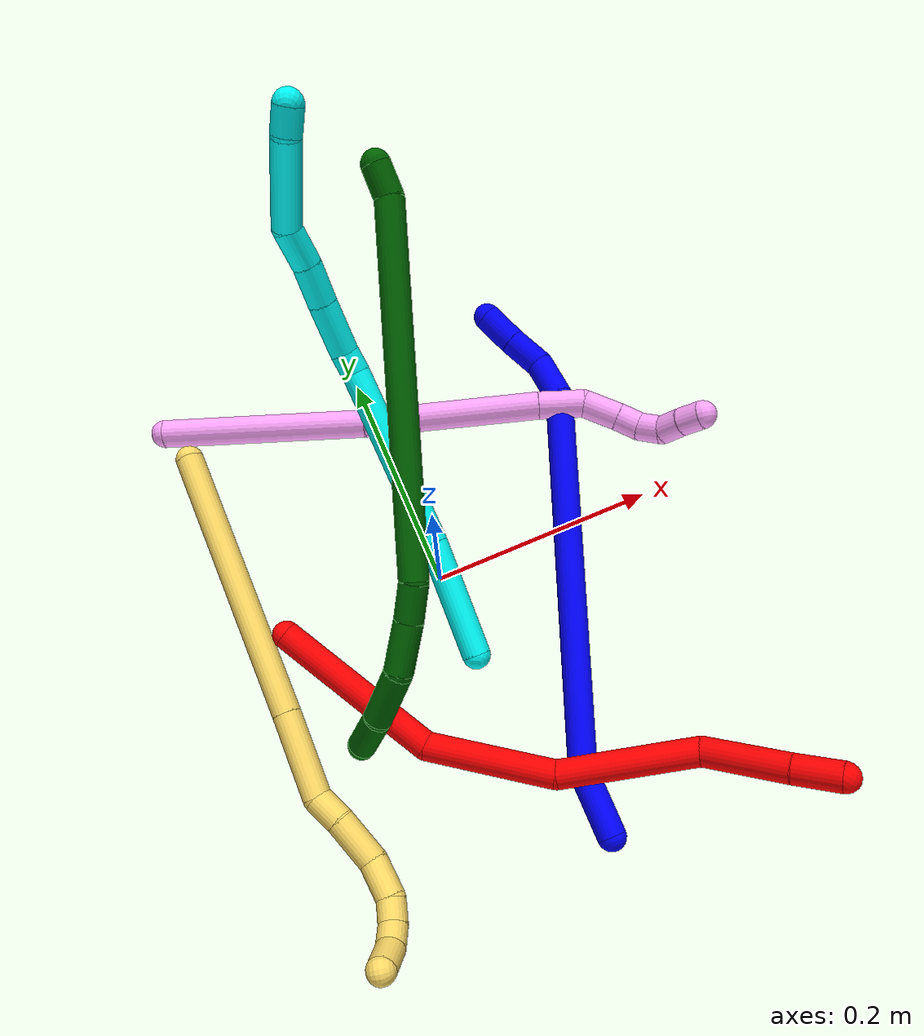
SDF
<sdf version="1.7">
 <world name="default">
  <plugin name="TubeGeneratorPlugin" filename="libtube_generator_plugin.so"/>
  <model name="photoneo_s_sensor">
   <static>1</static>
   <pose>0 0 2 1.57079 1.57079 3.14159</pose>
   <link name="link">
    <inertial><mass>0.1</mass></inertial>
    <sensor name="sensor" type="depth">
     <update_rate>30</update_rate>
     <camera>
      <horizontal_fov>1.22</horizontal_fov>
      <image><width>1920</width><height>1200</height><format>B8G8R8</format></image>
      <clip><near>0.1</near><far>4</far></clip>
      <depth_camera><output>points</output></depth_camera>
     </camera>
     <plugin name="camera_plugin" filename="libgazebo_ros_depth_camera.so">
      <baseline>0.2</baseline>
      <alwaysOn>1</alwaysOn>
      <updateRate>0.0</updateRate>
      <cameraName>camera_ir</cameraName>
      <imageTopicName>/camera/color/image_raw</imageTopicName>
      <cameraInfoTopicName>/camera/color/camera_info</cameraInfoTopicName>
      <depthImageTopicName>/camera/depth/image_raw</depthImageTopicName>
      <depthImageCameraInfoTopicName>/camera/depth/camera_info</depthImageCameraInfoTopicName>
      <pointCloudTopicName>/camera/depth/points</pointCloudTopicName>
      <frameName>fr_optical</frameName>
      <pointCloudCutoff>0.1</pointCloudCutoff>
      <pointCloudCutoffMax>2.0</pointCloudCutoffMax>
      <distortionK1>0</distortionK1>
      <distortionK2>0</distortionK2>
      <distortionK3>0</distortionK3>
      <distortionT1>0</distortionT1>
      <distortionT2>0</distortionT2>
      <CxPrime>0</CxPrime>
      <Cx>0</Cx>
      <Cy>0</Cy>
      <focalLength>0</focalLength>
      <hackBaseline>0</hackBaseline>
     </plugin>
    </sensor>
   </link>
  </model>
  <gravity>0 0 -9.8</gravity>
  <magnetic_field>6e-06 2.3e-05 -4.2e-05</magnetic_field>
  <atmosphere type="adiabatic"/>
  <physics name="default_physics" default="0" type="ode">
   <max_step_size>0.003</max_step_size>
   <real_time_factor>1</real_time_factor>
   <real_time_update_rate>1000</real_time_update_rate>
   <max_contacts>10000</max_contacts>
   <ode>
    <solver>
     <type>quick</type>
     <iters>100</iters>
     <sor>1.3</sor>
     <use_dynamic_moi_rescaling>0</use_dynamic_moi_rescaling>
    </solver>
    <constraints>
     <contact_max_correcting_vel>0</contact_max_correcting_vel>
     <contact_surface_layer>0.001</contact_surface_layer>
     <cfm>0</cfm>
     <erp>0.2</erp>
    </constraints>
   </ode>
  </physics>
  <scene><ambient>0.4 0.4 0.4 1</ambient><background>0.7 0.7 0.7 1</background><shadows>0</shadows></scene>
  <audio><device>default</device></audio>
  <spherical_coordinates>
   <surface_model>EARTH_WGS84</surface_model>
   <latitude_deg>0</latitude_deg>
   <longitude_deg>0</longitude_deg>
   <elevation>0</elevation>
   <heading_deg>0</heading_deg>
  </spherical_coordinates>
  <model name="bin">
   <static>1</static>
   <link name="bottom">
    <collision name="collision-bottom">
     <pose>0 0 -0.01 0 -0 0</pose>
     <geometry><box><size>0.8 0.6 0.02</size></box></geometry>
     <surface>
      <friction><ode><mu>100</mu><mu2>100</mu2></ode></friction>
      <contact><collide_bitmask>65535</collide_bitmask></contact>
     </surface>
    </collision>
   </link>
   <link name="west_wall">
    <collision name="collision-west_wall">
     <pose>-0.41 0 0.1 0 -0 0</pose>
     <geometry><box><size>0.02 0.6 0.2</size></box></geometry>
     <surface>
      <friction><ode><mu>100</mu><mu2>100</mu2></ode></friction>
      <contact><collide_bitmask>65535</collide_bitmask></contact>
     </surface>
    </collision>
   </link>
   <link name="east_wall">
    <collision name="collision-east_wall">
     <pose>0.41 0 0.1 0 -0 0</pose>
     <geometry><box><size>0.02 0.6 0.2</size></box></geometry>
     <surface>
      <friction><ode><mu>100</mu><mu2>100</mu2></ode></friction>
      <contact><collide_bitmask>65535</collide_bitmask></contact>
     </surface>
    </collision>
   </link>
   <link name="south_wall">
    <collision name="collision-south_wall">
     <pose>0 -0.31 0.1 0 -0 0</pose>
     <geometry><box><size>0.8 0.02 0.2</size></box></geometry>
     <surface>
      <friction><ode><mu>100</mu><mu2>100</mu2></ode></friction>
      <contact><collide_bitmask>65535</collide_bitmask></contact>
     </surface>
    </collision>
   </link>
   <link name="north_wall">
    <collision name="collision-north_wall">
     <pose>0 0.31 0.1 0 -0 0</pose>
     <geometry><box><size>0.8 0.02 0.2</size></box></geometry>
     <surface>
      <friction><ode><mu>100</mu><mu2>100</mu2></ode></friction>
      <contact><collide_bitmask>65535</collide_bitmask></contact>
     </surface>
    </collision>
   </link>
  </model>
  <model name="1">
   <static>0</static>
   <link name="1">
    <collision name="collision-cylinder-e_1_1_4">
     <pose>-0.001002 0.000346 0.029081 -0.011899 -0.034436 0.000205</pose>
     <geometry><cylinder><radius>0.0125</radius><length>0.058201</length></cylinder></geometry>
     <surface>
      <friction><ode><mu>1.16</mu><mu2>1.16</mu2><slip1>0</slip1><slip2>0</slip2></ode></friction>
      <contact><ode><kp>1e+06</kp><kd>1</kd><max_vel>0</max_vel><min_depth>0.001</min_depth></ode></contact>
     </surface>
    </collision>
    <visual name="visual-cylinder-e_1_1_4">
     <pose>-0.001002 0.000346 0.029081 -0.011899 -0.034436 0.000205</pose>
     <geometry><cylinder><radius>0.0125</radius><length>0.058201</length></cylinder></geometry>
     <material><ambient>0 0 1 1</ambient></material>
    </visual>
    <collision name="collision-cylinder-e_2_4_5">
     <pose>0.049859 0.017233 0.215816 -0.104536 0.316196 -0.016681</pose>
     <geometry><cylinder><radius>0.0125</radius><length>0.333575</length></cylinder></geometry>
     <surface>
      <friction><ode><mu>1.16</mu><mu2>1.16</mu2><slip1>0</slip1><slip2>0</slip2></ode></friction>
      <contact><ode><kp>1e+06</kp><kd>1</kd><max_vel>0</max_vel><min_depth>0.001</min_depth></ode></contact>
     </surface>
    </collision>
    <visual name="visual-cylinder-e_2_4_5">
     <pose>0.049859 0.017233 0.215816 -0.104536 0.316196 -0.016681</pose>
     <geometry><cylinder><radius>0.0125</radius><length>0.333575</length></cylinder></geometry>
     <material><ambient>0 0 1 1</ambient></material>
    </visual>
    <collision name="collision-cylinder-e_3_5_6">
     <pose>0.098798 0.038088 0.393471 -0.212479 -0.141961 0.015164</pose>
     <geometry><cylinder><radius>0.0125</radius><length>0.041338</length></cylinder></geometry>
     <surface>
      <friction><ode><mu>1.16</mu><mu2>1.16</mu2><slip1>0</slip1><slip2>0</slip2></ode></friction>
      <contact><ode><kp>1e+06</kp><kd>1</kd><max_vel>0</max_vel><min_depth>0.001</min_depth></ode></contact>
     </surface>
    </collision>
    <visual name="visual-cylinder-e_3_5_6">
     <pose>0.098798 0.038088 0.393471 -0.212479 -0.141961 0.015164</pose>
     <geometry><cylinder><radius>0.0125</radius><length>0.041338</length></cylinder></geometry>
     <material><ambient>0 0 1 1</ambient></material>
    </visual>
    <collision name="collision-cylinder-e_4_6_7">
     <pose>0.088992 0.03901 0.428486 0.222249 -0.420399 -0.047604</pose>
     <geometry><cylinder><radius>0.0125</radius><length>0.033723</length></cylinder></geometry>
     <surface>
      <friction><ode><mu>1.16</mu><mu2>1.16</mu2><slip1>0</slip1><slip2>0</slip2></ode></friction>
      <contact><ode><kp>1e+06</kp><kd>1</kd><max_vel>0</max_vel><min_depth>0.001</min_depth></ode></contact>
     </surface>
    </collision>
    <visual name="visual-cylinder-e_4_6_7">
     <pose>0.088992 0.03901 0.428486 0.222249 -0.420399 -0.047604</pose>
     <geometry><cylinder><radius>0.0125</radius><length>0.033723</length></cylinder></geometry>
     <material><ambient>0 0 1 1</ambient></material>
    </visual>
    <collision name="collision-cylinder-e_5_7_2">
     <pose>0.076365 0.032524 0.458745 0.200191 -0.353805 -0.035905</pose>
     <geometry><cylinder><radius>0.0125</radius><length>0.033163</length></cylinder></geometry>
     <surface>
      <friction><ode><mu>1.16</mu><mu2>1.16</mu2><slip1>0</slip1><slip2>0</slip2></ode></friction>
      <contact><ode><kp>1e+06</kp><kd>1</kd><max_vel>0</max_vel><min_depth>0.001</min_depth></ode></contact>
     </surface>
    </collision>
    <visual name="visual-cylinder-e_5_7_2">
     <pose>0.076365 0.032524 0.458745 0.200191 -0.353805 -0.035905</pose>
     <geometry><cylinder><radius>0.0125</radius><length>0.033163</length></cylinder></geometry>
     <material><ambient>0 0 1 1</ambient></material>
    </visual>
    <collision name="collision-sphere-2">
     <pose>0.07062 0.029431 0.473989 0 -0 0</pose>
     <geometry><sphere><radius>0.0125</radius></sphere></geometry>
     <surface>
      <friction><ode><mu>1.16</mu><mu2>1.16</mu2><slip1>0</slip1><slip2>0</slip2></ode></friction>
      <contact><ode><kp>1e+06</kp><kd>1</kd><max_vel>0</max_vel><min_depth>0.001</min_depth></ode></contact>
     </surface>
    </collision>
    <visual name="visual-sphere-2">
     <pose>0.07062 0.029431 0.473989 0 -0 0</pose>
     <geometry><sphere><radius>0.0125</radius></sphere></geometry>
     <material><ambient>0 0 1 1</ambient></material>
    </visual>
    <collision name="collision-sphere-7">
     <pose>0.08211 0.035617 0.443501 0 -0 0</pose>
     <geometry><sphere><radius>0.0125</radius></sphere></geometry>
     <surface>
      <friction><ode><mu>1.16</mu><mu2>1.16</mu2><slip1>0</slip1><slip2>0</slip2></ode></friction>
      <contact><ode><kp>1e+06</kp><kd>1</kd><max_vel>0</max_vel><min_depth>0.001</min_depth></ode></contact>
     </surface>
    </collision>
    <visual name="visual-sphere-7">
     <pose>0.08211 0.035617 0.443501 0 -0 0</pose>
     <geometry><sphere><radius>0.0125</radius></sphere></geometry>
     <material><ambient>0 0 1 1</ambient></material>
    </visual>
    <collision name="collision-sphere-6">
     <pose>0.095873 0.042403 0.413472 0 -0 0</pose>
     <geometry><sphere><radius>0.0125</radius></sphere></geometry>
     <surface>
      <friction><ode><mu>1.16</mu><mu2>1.16</mu2><slip1>0</slip1><slip2>0</slip2></ode></friction>
      <contact><ode><kp>1e+06</kp><kd>1</kd><max_vel>0</max_vel><min_depth>0.001</min_depth></ode></contact>
     </surface>
    </collision>
    <visual name="visual-sphere-6">
     <pose>0.095873 0.042403 0.413472 0 -0 0</pose>
     <geometry><sphere><radius>0.0125</radius></sphere></geometry>
     <material><ambient>0 0 1 1</ambient></material>
    </visual>
    <collision name="collision-sphere-5">
     <pose>0.101722 0.033774 0.37347 0 -0 0</pose>
     <geometry><sphere><radius>0.0125</radius></sphere></geometry>
     <surface>
      <friction><ode><mu>1.16</mu><mu2>1.16</mu2><slip1>0</slip1><slip2>0</slip2></ode></friction>
      <contact><ode><kp>1e+06</kp><kd>1</kd><max_vel>0</max_vel><min_depth>0.001</min_depth></ode></contact>
     </surface>
    </collision>
    <visual name="visual-sphere-5">
     <pose>0.101722 0.033774 0.37347 0 -0 0</pose>
     <geometry><sphere><radius>0.0125</radius></sphere></geometry>
     <material><ambient>0 0 1 1</ambient></material>
    </visual>
    <collision name="collision-sphere-1">
     <geometry><sphere><radius>0.0125</radius></sphere></geometry>
     <surface>
      <friction><ode><mu>1.16</mu><mu2>1.16</mu2><slip1>0</slip1><slip2>0</slip2></ode></friction>
      <contact><ode><kp>1e+06</kp><kd>1</kd><max_vel>0</max_vel><min_depth>0.001</min_depth></ode></contact>
     </surface>
    </collision>
    <visual name="visual-sphere-1">
     <geometry><sphere><radius>0.0125</radius></sphere></geometry>
     <material><ambient>0 0 1 1</ambient></material>
    </visual>
    <collision name="collision-sphere-4">
     <pose>-0.002004 0.000692 0.058163 0 -0 0</pose>
     <geometry><sphere><radius>0.0125</radius></sphere></geometry>
     <surface>
      <friction><ode><mu>1.16</mu><mu2>1.16</mu2><slip1>0</slip1><slip2>0</slip2></ode></friction>
      <contact><ode><kp>1e+06</kp><kd>1</kd><max_vel>0</max_vel><min_depth>0.001</min_depth></ode></contact>
     </surface>
    </collision>
    <visual name="visual-sphere-4">
     <pose>-0.002004 0.000692 0.058163 0 -0 0</pose>
     <geometry><sphere><radius>0.0125</radius></sphere></geometry>
     <material><ambient>0 0 1 1</ambient></material>
    </visual>
    <inertial>
     <pose>0.052382 0.019474 0.239224 0 -0 0</pose>
     <mass>0.5</mass>
     <inertia>
      <ixx>0.002942</ixx>
      <ixy>0</ixy>
      <ixz>0</ixz>
      <iyy>0.003078</iyy>
      <iyz>0</iyz>
      <izz>-0.001232</izz>
     </inertia>
    </inertial>
   </link>
   <pose>0.045534 -0.261765 0.011474 -1.54544 -0.373732 -0.039487</pose>
  </model>
  <model name="2">
   <static>0</static>
   <link name="2">
    <collision name="collision-cylinder-e_1_1_4">
     <pose>-0.005512 0.004189 0.07675 -0.054523 -0.071584 0.001953</pose>
     <geometry><cylinder><radius>0.0125</radius><length>0.154123</length></cylinder></geometry>
     <surface>
      <friction><ode><mu>1.16</mu><mu2>1.16</mu2><slip1>0</slip1><slip2>0</slip2></ode></friction>
      <contact><ode><kp>1e+06</kp><kd>1</kd><max_vel>0</max_vel><min_depth>0.001</min_depth></ode></contact>
     </surface>
    </collision>
    <visual name="visual-cylinder-e_1_1_4">
     <pose>-0.005512 0.004189 0.07675 -0.054523 -0.071584 0.001953</pose>
     <geometry><cylinder><radius>0.0125</radius><length>0.154123</length></cylinder></geometry>
     <material><ambient>1 0 0 1</ambient></material>
    </visual>
    <collision name="collision-cylinder-e_2_4_5">
     <pose>0.010562 0.00473 0.205711 0.069759 0.391175 0.013826</pose>
     <geometry><cylinder><radius>0.0125</radius><length>0.113229</length></cylinder></geometry>
     <surface>
      <friction><ode><mu>1.16</mu><mu2>1.16</mu2><slip1>0</slip1><slip2>0</slip2></ode></friction>
      <contact><ode><kp>1e+06</kp><kd>1</kd><max_vel>0</max_vel><min_depth>0.001</min_depth></ode></contact>
     </surface>
    </collision>
    <visual name="visual-cylinder-e_2_4_5">
     <pose>0.010562 0.00473 0.205711 0.069759 0.391175 0.013826</pose>
     <geometry><cylinder><radius>0.0125</radius><length>0.113229</length></cylinder></geometry>
     <material><ambient>1 0 0 1</ambient></material>
    </visual>
    <collision name="collision-cylinder-e_3_5_6">
     <pose>0.069787 -0.014288 0.301711 0.337545 0.681441 0.120679</pose>
     <geometry><cylinder><radius>0.0125</radius><length>0.119505</length></cylinder></geometry>
     <surface>
      <friction><ode><mu>1.16</mu><mu2>1.16</mu2><slip1>0</slip1><slip2>0</slip2></ode></friction>
      <contact><ode><kp>1e+06</kp><kd>1</kd><max_vel>0</max_vel><min_depth>0.001</min_depth></ode></contact>
     </surface>
    </collision>
    <visual name="visual-cylinder-e_3_5_6">
     <pose>0.069787 -0.014288 0.301711 0.337545 0.681441 0.120679</pose>
     <geometry><cylinder><radius>0.0125</radius><length>0.119505</length></cylinder></geometry>
     <material><ambient>1 0 0 1</ambient></material>
    </visual>
    <collision name="collision-cylinder-e_4_6_7">
     <pose>0.127453 -0.021565 0.375608 -0.262536 0.571003 -0.077466</pose>
     <geometry><cylinder><radius>0.0125</radius><length>0.074109</length></cylinder></geometry>
     <surface>
      <friction><ode><mu>1.16</mu><mu2>1.16</mu2><slip1>0</slip1><slip2>0</slip2></ode></friction>
      <contact><ode><kp>1e+06</kp><kd>1</kd><max_vel>0</max_vel><min_depth>0.001</min_depth></ode></contact>
     </surface>
    </collision>
    <visual name="visual-cylinder-e_4_6_7">
     <pose>0.127453 -0.021565 0.375608 -0.262536 0.571003 -0.077466</pose>
     <geometry><cylinder><radius>0.0125</radius><length>0.074109</length></cylinder></geometry>
     <material><ambient>1 0 0 1</ambient></material>
    </visual>
    <collision name="collision-cylinder-e_5_7_2">
     <pose>0.158024 -0.010706 0.421904 -0.169351 0.570711 -0.04979</pose>
     <geometry><cylinder><radius>0.0125</radius><length>0.039033</length></cylinder></geometry>
     <surface>
      <friction><ode><mu>1.16</mu><mu2>1.16</mu2><slip1>0</slip1><slip2>0</slip2></ode></friction>
      <contact><ode><kp>1e+06</kp><kd>1</kd><max_vel>0</max_vel><min_depth>0.001</min_depth></ode></contact>
     </surface>
    </collision>
    <visual name="visual-cylinder-e_5_7_2">
     <pose>0.158024 -0.010706 0.421904 -0.169351 0.570711 -0.04979</pose>
     <geometry><cylinder><radius>0.0125</radius><length>0.039033</length></cylinder></geometry>
     <material><ambient>1 0 0 1</ambient></material>
    </visual>
    <collision name="collision-sphere-2">
     <pose>0.168567 -0.007938 0.438093 0 -0 0</pose>
     <geometry><sphere><radius>0.0125</radius></sphere></geometry>
     <surface>
      <friction><ode><mu>1.16</mu><mu2>1.16</mu2><slip1>0</slip1><slip2>0</slip2></ode></friction>
      <contact><ode><kp>1e+06</kp><kd>1</kd><max_vel>0</max_vel><min_depth>0.001</min_depth></ode></contact>
     </surface>
    </collision>
    <visual name="visual-sphere-2">
     <pose>0.168567 -0.007938 0.438093 0 -0 0</pose>
     <geometry><sphere><radius>0.0125</radius></sphere></geometry>
     <material><ambient>1 0 0 1</ambient></material>
    </visual>
    <collision name="collision-sphere-7">
     <pose>0.14748 -0.013474 0.405716 0 -0 0</pose>
     <geometry><sphere><radius>0.0125</radius></sphere></geometry>
     <surface>
      <friction><ode><mu>1.16</mu><mu2>1.16</mu2><slip1>0</slip1><slip2>0</slip2></ode></friction>
      <contact><ode><kp>1e+06</kp><kd>1</kd><max_vel>0</max_vel><min_depth>0.001</min_depth></ode></contact>
     </surface>
    </collision>
    <visual name="visual-sphere-7">
     <pose>0.14748 -0.013474 0.405716 0 -0 0</pose>
     <geometry><sphere><radius>0.0125</radius></sphere></geometry>
     <material><ambient>1 0 0 1</ambient></material>
    </visual>
    <collision name="collision-sphere-6">
     <pose>0.107426 -0.029657 0.3455 0 -0 0</pose>
     <geometry><sphere><radius>0.0125</radius></sphere></geometry>
     <surface>
      <friction><ode><mu>1.16</mu><mu2>1.16</mu2><slip1>0</slip1><slip2>0</slip2></ode></friction>
      <contact><ode><kp>1e+06</kp><kd>1</kd><max_vel>0</max_vel><min_depth>0.001</min_depth></ode></contact>
     </surface>
    </collision>
    <visual name="visual-sphere-6">
     <pose>0.107426 -0.029657 0.3455 0 -0 0</pose>
     <geometry><sphere><radius>0.0125</radius></sphere></geometry>
     <material><ambient>1 0 0 1</ambient></material>
    </visual>
    <collision name="collision-sphere-5">
     <pose>0.032148 0.001081 0.257922 0 -0 0</pose>
     <geometry><sphere><radius>0.0125</radius></sphere></geometry>
     <surface>
      <friction><ode><mu>1.16</mu><mu2>1.16</mu2><slip1>0</slip1><slip2>0</slip2></ode></friction>
      <contact><ode><kp>1e+06</kp><kd>1</kd><max_vel>0</max_vel><min_depth>0.001</min_depth></ode></contact>
     </surface>
    </collision>
    <visual name="visual-sphere-5">
     <pose>0.032148 0.001081 0.257922 0 -0 0</pose>
     <geometry><sphere><radius>0.0125</radius></sphere></geometry>
     <material><ambient>1 0 0 1</ambient></material>
    </visual>
    <collision name="collision-sphere-1">
     <geometry><sphere><radius>0.0125</radius></sphere></geometry>
     <surface>
      <friction><ode><mu>1.16</mu><mu2>1.16</mu2><slip1>0</slip1><slip2>0</slip2></ode></friction>
      <contact><ode><kp>1e+06</kp><kd>1</kd><max_vel>0</max_vel><min_depth>0.001</min_depth></ode></contact>
     </surface>
    </collision>
    <visual name="visual-sphere-1">
     <geometry><sphere><radius>0.0125</radius></sphere></geometry>
     <material><ambient>1 0 0 1</ambient></material>
    </visual>
    <collision name="collision-sphere-4">
     <pose>-0.011023 0.008378 0.1535 0 -0 0</pose>
     <geometry><sphere><radius>0.0125</radius></sphere></geometry>
     <surface>
      <friction><ode><mu>1.16</mu><mu2>1.16</mu2><slip1>0</slip1><slip2>0</slip2></ode></friction>
      <contact><ode><kp>1e+06</kp><kd>1</kd><max_vel>0</max_vel><min_depth>0.001</min_depth></ode></contact>
     </surface>
    </collision>
    <visual name="visual-sphere-4">
     <pose>-0.011023 0.008378 0.1535 0 -0 0</pose>
     <geometry><sphere><radius>0.0125</radius></sphere></geometry>
     <material><ambient>1 0 0 1</ambient></material>
    </visual>
    <inertial>
     <pose>0.0486 -0.005085 0.230963 0 -0 0</pose>
     <mass>0.5</mass>
     <inertia>
      <ixx>0.000602</ixx>
      <ixy>0</ixy>
      <ixz>0</ixz>
      <iyy>0.000632</iyy>
      <iyz>0</iyz>
      <izz>-8.7e-05</izz>
     </inertia>
    </inertial>
   </link>
   <pose>-0.142626 0.002413 0.017612 1.60759 -0.706862 0.571937</pose>
  </model>
  <model name="3">
   <static>0</static>
   <link name="3">
    <collision name="collision-cylinder-e_1_1_4">
     <pose>-0.021721 0.026399 0.039145 -0.59333 -0.431173 0.133685</pose>
     <geometry><cylinder><radius>0.0125</radius><length>0.103944</length></cylinder></geometry>
     <surface>
      <friction><ode><mu>1.16</mu><mu2>1.16</mu2><slip1>0</slip1><slip2>0</slip2></ode></friction>
      <contact><ode><kp>1e+06</kp><kd>1</kd><max_vel>0</max_vel><min_depth>0.001</min_depth></ode></contact>
     </surface>
    </collision>
    <visual name="visual-cylinder-e_1_1_4">
     <pose>-0.021721 0.026399 0.039145 -0.59333 -0.431173 0.133685</pose>
     <geometry><cylinder><radius>0.0125</radius><length>0.103944</length></cylinder></geometry>
     <material><ambient>0.003922 1 0.996078 1</ambient></material>
    </visual>
    <collision name="collision-cylinder-e_2_4_5">
     <pose>-0.056556 0.069967 0.099634 -0.677416 -0.446521 0.159629</pose>
     <geometry><cylinder><radius>0.0125</radius><length>0.060738</length></cylinder></geometry>
     <surface>
      <friction><ode><mu>1.16</mu><mu2>1.16</mu2><slip1>0</slip1><slip2>0</slip2></ode></friction>
      <contact><ode><kp>1e+06</kp><kd>1</kd><max_vel>0</max_vel><min_depth>0.001</min_depth></ode></contact>
     </surface>
    </collision>
    <visual name="visual-cylinder-e_2_4_5">
     <pose>-0.056556 0.069967 0.099634 -0.677416 -0.446521 0.159629</pose>
     <geometry><cylinder><radius>0.0125</radius><length>0.060738</length></cylinder></geometry>
     <material><ambient>0.003922 1 0.996078 1</ambient></material>
    </visual>
    <collision name="collision-cylinder-e_3_5_6">
     <pose>-0.091168 0.115599 0.156275 -0.678638 -0.442717 0.158536</pose>
     <geometry><cylinder><radius>0.0125</radius><length>0.100364</length></cylinder></geometry>
     <surface>
      <friction><ode><mu>1.16</mu><mu2>1.16</mu2><slip1>0</slip1><slip2>0</slip2></ode></friction>
      <contact><ode><kp>1e+06</kp><kd>1</kd><max_vel>0</max_vel><min_depth>0.001</min_depth></ode></contact>
     </surface>
    </collision>
    <visual name="visual-cylinder-e_3_5_6">
     <pose>-0.091168 0.115599 0.156275 -0.678638 -0.442717 0.158536</pose>
     <geometry><cylinder><radius>0.0125</radius><length>0.100364</length></cylinder></geometry>
     <material><ambient>0.003922 1 0.996078 1</ambient></material>
    </visual>
    <collision name="collision-cylinder-e_4_6_7">
     <pose>-0.118799 0.150633 0.196464 -0.930723 -0.642686 0.331246</pose>
     <geometry><cylinder><radius>0.0125</radius><length>0.020465</length></cylinder></geometry>
     <surface>
      <friction><ode><mu>1.16</mu><mu2>1.16</mu2><slip1>0</slip1><slip2>0</slip2></ode></friction>
      <contact><ode><kp>1e+06</kp><kd>1</kd><max_vel>0</max_vel><min_depth>0.001</min_depth></ode></contact>
     </surface>
    </collision>
    <visual name="visual-cylinder-e_4_6_7">
     <pose>-0.118799 0.150633 0.196464 -0.930723 -0.642686 0.331246</pose>
     <geometry><cylinder><radius>0.0125</radius><length>0.020465</length></cylinder></geometry>
     <material><ambient>0.003922 1 0.996078 1</ambient></material>
    </visual>
    <collision name="collision-cylinder-e_5_7_8">
     <pose>-0.142069 0.170055 0.209764 -0.991462 -0.840079 0.473962</pose>
     <geometry><cylinder><radius>0.0125</radius><length>0.046024</length></cylinder></geometry>
     <surface>
      <friction><ode><mu>1.16</mu><mu2>1.16</mu2><slip1>0</slip1><slip2>0</slip2></ode></friction>
      <contact><ode><kp>1e+06</kp><kd>1</kd><max_vel>0</max_vel><min_depth>0.001</min_depth></ode></contact>
     </surface>
    </collision>
    <visual name="visual-cylinder-e_5_7_8">
     <pose>-0.142069 0.170055 0.209764 -0.991462 -0.840079 0.473962</pose>
     <geometry><cylinder><radius>0.0125</radius><length>0.046024</length></cylinder></geometry>
     <material><ambient>0.003922 1 0.996078 1</ambient></material>
    </visual>
    <collision name="collision-cylinder-e_6_8_9">
     <pose>-0.173013 0.192014 0.223643 -1.02984 -0.914983 0.543379</pose>
     <geometry><cylinder><radius>0.0125</radius><length>0.034843</length></cylinder></geometry>
     <surface>
      <friction><ode><mu>1.16</mu><mu2>1.16</mu2><slip1>0</slip1><slip2>0</slip2></ode></friction>
      <contact><ode><kp>1e+06</kp><kd>1</kd><max_vel>0</max_vel><min_depth>0.001</min_depth></ode></contact>
     </surface>
    </collision>
    <visual name="visual-cylinder-e_6_8_9">
     <pose>-0.173013 0.192014 0.223643 -1.02984 -0.914983 0.543379</pose>
     <geometry><cylinder><radius>0.0125</radius><length>0.034843</length></cylinder></geometry>
     <material><ambient>0.003922 1 0.996078 1</ambient></material>
    </visual>
    <collision name="collision-cylinder-e_7_9_10">
     <pose>-0.200093 0.211324 0.232534 -1.2474 -0.889505 0.660705</pose>
     <geometry><cylinder><radius>0.0125</radius><length>0.034173</length></cylinder></geometry>
     <surface>
      <friction><ode><mu>1.16</mu><mu2>1.16</mu2><slip1>0</slip1><slip2>0</slip2></ode></friction>
      <contact><ode><kp>1e+06</kp><kd>1</kd><max_vel>0</max_vel><min_depth>0.001</min_depth></ode></contact>
     </surface>
    </collision>
    <visual name="visual-cylinder-e_7_9_10">
     <pose>-0.200093 0.211324 0.232534 -1.2474 -0.889505 0.660705</pose>
     <geometry><cylinder><radius>0.0125</radius><length>0.034173</length></cylinder></geometry>
     <material><ambient>0.003922 1 0.996078 1</ambient></material>
    </visual>
    <collision name="collision-cylinder-e_8_10_11">
     <pose>-0.250819 0.226909 0.241874 -0.73772 -1.36035 0.606135</pose>
     <geometry><cylinder><radius>0.0125</radius><length>0.076597</length></cylinder></geometry>
     <surface>
      <friction><ode><mu>1.16</mu><mu2>1.16</mu2><slip1>0</slip1><slip2>0</slip2></ode></friction>
      <contact><ode><kp>1e+06</kp><kd>1</kd><max_vel>0</max_vel><min_depth>0.001</min_depth></ode></contact>
     </surface>
    </collision>
    <visual name="visual-cylinder-e_8_10_11">
     <pose>-0.250819 0.226909 0.241874 -0.73772 -1.36035 0.606135</pose>
     <geometry><cylinder><radius>0.0125</radius><length>0.076597</length></cylinder></geometry>
     <material><ambient>0.003922 1 0.996078 1</ambient></material>
    </visual>
    <collision name="collision-cylinder-e_9_11_2">
     <pose>-0.29866 0.233258 0.252453 -0.204916 -1.14125 0.131797</pose>
     <geometry><cylinder><radius>0.0125</radius><length>0.022851</length></cylinder></geometry>
     <surface>
      <friction><ode><mu>1.16</mu><mu2>1.16</mu2><slip1>0</slip1><slip2>0</slip2></ode></friction>
      <contact><ode><kp>1e+06</kp><kd>1</kd><max_vel>0</max_vel><min_depth>0.001</min_depth></ode></contact>
     </surface>
    </collision>
    <visual name="visual-cylinder-e_9_11_2">
     <pose>-0.29866 0.233258 0.252453 -0.204916 -1.14125 0.131797</pose>
     <geometry><cylinder><radius>0.0125</radius><length>0.022851</length></cylinder></geometry>
     <material><ambient>0.003922 1 0.996078 1</ambient></material>
    </visual>
    <collision name="collision-sphere-2">
     <pose>-0.309048 0.234226 0.257112 0 -0 0</pose>
     <geometry><sphere><radius>0.0125</radius></sphere></geometry>
     <surface>
      <friction><ode><mu>1.16</mu><mu2>1.16</mu2><slip1>0</slip1><slip2>0</slip2></ode></friction>
      <contact><ode><kp>1e+06</kp><kd>1</kd><max_vel>0</max_vel><min_depth>0.001</min_depth></ode></contact>
     </surface>
    </collision>
    <visual name="visual-sphere-2">
     <pose>-0.309048 0.234226 0.257112 0 -0 0</pose>
     <geometry><sphere><radius>0.0125</radius></sphere></geometry>
     <material><ambient>0.003922 1 0.996078 1</ambient></material>
    </visual>
    <collision name="collision-sphere-11">
     <pose>-0.288272 0.23229 0.247794 0 -0 0</pose>
     <geometry><sphere><radius>0.0125</radius></sphere></geometry>
     <surface>
      <friction><ode><mu>1.16</mu><mu2>1.16</mu2><slip1>0</slip1><slip2>0</slip2></ode></friction>
      <contact><ode><kp>1e+06</kp><kd>1</kd><max_vel>0</max_vel><min_depth>0.001</min_depth></ode></contact>
     </surface>
    </collision>
    <visual name="visual-sphere-11">
     <pose>-0.288272 0.23229 0.247794 0 -0 0</pose>
     <geometry><sphere><radius>0.0125</radius></sphere></geometry>
     <material><ambient>0.003922 1 0.996078 1</ambient></material>
    </visual>
    <collision name="collision-sphere-10">
     <pose>-0.213365 0.221527 0.235953 0 -0 0</pose>
     <geometry><sphere><radius>0.0125</radius></sphere></geometry>
     <surface>
      <friction><ode><mu>1.16</mu><mu2>1.16</mu2><slip1>0</slip1><slip2>0</slip2></ode></friction>
      <contact><ode><kp>1e+06</kp><kd>1</kd><max_vel>0</max_vel><min_depth>0.001</min_depth></ode></contact>
     </surface>
    </collision>
    <visual name="visual-sphere-10">
     <pose>-0.213365 0.221527 0.235953 0 -0 0</pose>
     <geometry><sphere><radius>0.0125</radius></sphere></geometry>
     <material><ambient>0.003922 1 0.996078 1</ambient></material>
    </visual>
    <collision name="collision-sphere-9">
     <pose>-0.186821 0.201121 0.229114 0 -0 0</pose>
     <geometry><sphere><radius>0.0125</radius></sphere></geometry>
     <surface>
      <friction><ode><mu>1.16</mu><mu2>1.16</mu2><slip1>0</slip1><slip2>0</slip2></ode></friction>
      <contact><ode><kp>1e+06</kp><kd>1</kd><max_vel>0</max_vel><min_depth>0.001</min_depth></ode></contact>
     </surface>
    </collision>
    <visual name="visual-sphere-9">
     <pose>-0.186821 0.201121 0.229114 0 -0 0</pose>
     <geometry><sphere><radius>0.0125</radius></sphere></geometry>
     <material><ambient>0.003922 1 0.996078 1</ambient></material>
    </visual>
    <collision name="collision-sphere-4">
     <pose>-0.043442 0.052799 0.078291 0 -0 0</pose>
     <geometry><sphere><radius>0.0125</radius></sphere></geometry>
     <surface>
      <friction><ode><mu>1.16</mu><mu2>1.16</mu2><slip1>0</slip1><slip2>0</slip2></ode></friction>
      <contact><ode><kp>1e+06</kp><kd>1</kd><max_vel>0</max_vel><min_depth>0.001</min_depth></ode></contact>
     </surface>
    </collision>
    <visual name="visual-sphere-4">
     <pose>-0.043442 0.052799 0.078291 0 -0 0</pose>
     <geometry><sphere><radius>0.0125</radius></sphere></geometry>
     <material><ambient>0.003922 1 0.996078 1</ambient></material>
    </visual>
    <collision name="collision-sphere-1">
     <geometry><sphere><radius>0.0125</radius></sphere></geometry>
     <surface>
      <friction><ode><mu>1.16</mu><mu2>1.16</mu2><slip1>0</slip1><slip2>0</slip2></ode></friction>
      <contact><ode><kp>1e+06</kp><kd>1</kd><max_vel>0</max_vel><min_depth>0.001</min_depth></ode></contact>
     </surface>
    </collision>
    <visual name="visual-sphere-1">
     <geometry><sphere><radius>0.0125</radius></sphere></geometry>
     <material><ambient>0.003922 1 0.996078 1</ambient></material>
    </visual>
    <collision name="collision-sphere-8">
     <pose>-0.159206 0.182907 0.218172 0 -0 0</pose>
     <geometry><sphere><radius>0.0125</radius></sphere></geometry>
     <surface>
      <friction><ode><mu>1.16</mu><mu2>1.16</mu2><slip1>0</slip1><slip2>0</slip2></ode></friction>
      <contact><ode><kp>1e+06</kp><kd>1</kd><max_vel>0</max_vel><min_depth>0.001</min_depth></ode></contact>
     </surface>
    </collision>
    <visual name="visual-sphere-8">
     <pose>-0.159206 0.182907 0.218172 0 -0 0</pose>
     <geometry><sphere><radius>0.0125</radius></sphere></geometry>
     <material><ambient>0.003922 1 0.996078 1</ambient></material>
    </visual>
    <collision name="collision-sphere-5">
     <pose>-0.06967 0.087135 0.120977 0 -0 0</pose>
     <geometry><sphere><radius>0.0125</radius></sphere></geometry>
     <surface>
      <friction><ode><mu>1.16</mu><mu2>1.16</mu2><slip1>0</slip1><slip2>0</slip2></ode></friction>
      <contact><ode><kp>1e+06</kp><kd>1</kd><max_vel>0</max_vel><min_depth>0.001</min_depth></ode></contact>
     </surface>
    </collision>
    <visual name="visual-sphere-5">
     <pose>-0.06967 0.087135 0.120977 0 -0 0</pose>
     <geometry><sphere><radius>0.0125</radius></sphere></geometry>
     <material><ambient>0.003922 1 0.996078 1</ambient></material>
    </visual>
    <collision name="collision-sphere-6">
     <pose>-0.112666 0.144063 0.191572 0 -0 0</pose>
     <geometry><sphere><radius>0.0125</radius></sphere></geometry>
     <surface>
      <friction><ode><mu>1.16</mu><mu2>1.16</mu2><slip1>0</slip1><slip2>0</slip2></ode></friction>
      <contact><ode><kp>1e+06</kp><kd>1</kd><max_vel>0</max_vel><min_depth>0.001</min_depth></ode></contact>
     </surface>
    </collision>
    <visual name="visual-sphere-6">
     <pose>-0.112666 0.144063 0.191572 0 -0 0</pose>
     <geometry><sphere><radius>0.0125</radius></sphere></geometry>
     <material><ambient>0.003922 1 0.996078 1</ambient></material>
    </visual>
    <collision name="collision-sphere-7">
     <pose>-0.124932 0.157203 0.201356 0 -0 0</pose>
     <geometry><sphere><radius>0.0125</radius></sphere></geometry>
     <surface>
      <friction><ode><mu>1.16</mu><mu2>1.16</mu2><slip1>0</slip1><slip2>0</slip2></ode></friction>
      <contact><ode><kp>1e+06</kp><kd>1</kd><max_vel>0</max_vel><min_depth>0.001</min_depth></ode></contact>
     </surface>
    </collision>
    <visual name="visual-sphere-7">
     <pose>-0.124932 0.157203 0.201356 0 -0 0</pose>
     <geometry><sphere><radius>0.0125</radius></sphere></geometry>
     <material><ambient>0.003922 1 0.996078 1</ambient></material>
    </visual>
    <inertial>
     <pose>-0.125431 0.132256 0.159029 0 -0 0</pose>
     <mass>0.5</mass>
     <inertia><ixx>0.00022</ixx><ixy>0</ixy><ixz>0</ixz><iyy>0.000287</iyy><iyz>0</iyz><izz>3.6e-05</izz></inertia>
    </inertial>
   </link>
   <pose>0.002074 -0.077161 0.011492 2.57264 1.14494 -2.62744</pose>
  </model>
  <model name="4">
   <static>0</static>
   <link name="4">
    <collision name="collision-cylinder-e_1_1_4">
     <pose>0.089773 0.014022 0.013473 -0.805356 1.35748 -0.661864</pose>
     <geometry><cylinder><radius>0.0125</radius><length>0.18371</length></cylinder></geometry>
     <surface>
      <friction><ode><mu>1.16</mu><mu2>1.16</mu2><slip1>0</slip1><slip2>0</slip2></ode></friction>
      <contact><ode><kp>1e+06</kp><kd>1</kd><max_vel>0</max_vel><min_depth>0.001</min_depth></ode></contact>
     </surface>
    </collision>
    <visual name="visual-cylinder-e_1_1_4">
     <pose>0.089773 0.014022 0.013473 -0.805356 1.35748 -0.661864</pose>
     <geometry><cylinder><radius>0.0125</radius><length>0.18371</length></cylinder></geometry>
     <material><ambient>1 0.65098 0.996078 1</ambient></material>
    </visual>
    <collision name="collision-cylinder-e_2_4_5">
     <pose>0.257424 0.038102 0.033979 -0.960583 1.41448 -0.837886</pose>
     <geometry><cylinder><radius>0.0125</radius><length>0.157678</length></cylinder></geometry>
     <surface>
      <friction><ode><mu>1.16</mu><mu2>1.16</mu2><slip1>0</slip1><slip2>0</slip2></ode></friction>
      <contact><ode><kp>1e+06</kp><kd>1</kd><max_vel>0</max_vel><min_depth>0.001</min_depth></ode></contact>
     </surface>
    </collision>
    <visual name="visual-cylinder-e_2_4_5">
     <pose>0.257424 0.038102 0.033979 -0.960583 1.41448 -0.837886</pose>
     <geometry><cylinder><radius>0.0125</radius><length>0.157678</length></cylinder></geometry>
     <material><ambient>1 0.65098 0.996078 1</ambient></material>
    </visual>
    <collision name="collision-cylinder-e_3_5_6">
     <pose>0.355517 0.050403 0.043936 -0.654278 1.39051 -0.551714</pose>
     <geometry><cylinder><radius>0.0125</radius><length>0.041097</length></cylinder></geometry>
     <surface>
      <friction><ode><mu>1.16</mu><mu2>1.16</mu2><slip1>0</slip1><slip2>0</slip2></ode></friction>
      <contact><ode><kp>1e+06</kp><kd>1</kd><max_vel>0</max_vel><min_depth>0.001</min_depth></ode></contact>
     </surface>
    </collision>
    <visual name="visual-cylinder-e_3_5_6">
     <pose>0.355517 0.050403 0.043936 -0.654278 1.39051 -0.551714</pose>
     <geometry><cylinder><radius>0.0125</radius><length>0.041097</length></cylinder></geometry>
     <material><ambient>1 0.65098 0.996078 1</ambient></material>
    </visual>
    <collision name="collision-cylinder-e_4_6_7">
     <pose>0.389403 0.055108 0.056036 -0.262188 0.963411 -0.13764</pose>
     <geometry><cylinder><radius>0.0125</radius><length>0.033296</length></cylinder></geometry>
     <surface>
      <friction><ode><mu>1.16</mu><mu2>1.16</mu2><slip1>0</slip1><slip2>0</slip2></ode></friction>
      <contact><ode><kp>1e+06</kp><kd>1</kd><max_vel>0</max_vel><min_depth>0.001</min_depth></ode></contact>
     </surface>
    </collision>
    <visual name="visual-cylinder-e_4_6_7">
     <pose>0.389403 0.055108 0.056036 -0.262188 0.963411 -0.13764</pose>
     <geometry><cylinder><radius>0.0125</radius><length>0.033296</length></cylinder></geometry>
     <material><ambient>1 0.65098 0.996078 1</ambient></material>
    </visual>
    <collision name="collision-cylinder-e_5_7_8">
     <pose>0.411371 0.059747 0.07173 -0.322302 0.879175 -0.1526</pose>
     <geometry><cylinder><radius>0.0125</radius><length>0.021547</length></cylinder></geometry>
     <surface>
      <friction><ode><mu>1.16</mu><mu2>1.16</mu2><slip1>0</slip1><slip2>0</slip2></ode></friction>
      <contact><ode><kp>1e+06</kp><kd>1</kd><max_vel>0</max_vel><min_depth>0.001</min_depth></ode></contact>
     </surface>
    </collision>
    <visual name="visual-cylinder-e_5_7_8">
     <pose>0.411371 0.059747 0.07173 -0.322302 0.879175 -0.1526</pose>
     <geometry><cylinder><radius>0.0125</radius><length>0.021547</length></cylinder></geometry>
     <material><ambient>1 0.65098 0.996078 1</ambient></material>
    </visual>
    <collision name="collision-cylinder-e_6_8_9">
     <pose>0.427626 0.068068 0.082536 -0.961407 0.815439 -0.443104</pose>
     <geometry><cylinder><radius>0.0125</radius><length>0.021859</length></cylinder></geometry>
     <surface>
      <friction><ode><mu>1.16</mu><mu2>1.16</mu2><slip1>0</slip1><slip2>0</slip2></ode></friction>
      <contact><ode><kp>1e+06</kp><kd>1</kd><max_vel>0</max_vel><min_depth>0.001</min_depth></ode></contact>
     </surface>
    </collision>
    <visual name="visual-cylinder-e_6_8_9">
     <pose>0.427626 0.068068 0.082536 -0.961407 0.815439 -0.443104</pose>
     <geometry><cylinder><radius>0.0125</radius><length>0.021859</length></cylinder></geometry>
     <material><ambient>1 0.65098 0.996078 1</ambient></material>
    </visual>
    <collision name="collision-cylinder-e_7_9_10">
     <pose>0.442424 0.08172 0.08602 -1.67762 0.736088 -0.810807</pose>
     <geometry><cylinder><radius>0.0125</radius><length>0.020379</length></cylinder></geometry>
     <surface>
      <friction><ode><mu>1.16</mu><mu2>1.16</mu2><slip1>0</slip1><slip2>0</slip2></ode></friction>
      <contact><ode><kp>1e+06</kp><kd>1</kd><max_vel>0</max_vel><min_depth>0.001</min_depth></ode></contact>
     </surface>
    </collision>
    <visual name="visual-cylinder-e_7_9_10">
     <pose>0.442424 0.08172 0.08602 -1.67762 0.736088 -0.810807</pose>
     <geometry><cylinder><radius>0.0125</radius><length>0.020379</length></cylinder></geometry>
     <material><ambient>1 0.65098 0.996078 1</ambient></material>
    </visual>
    <collision name="collision-cylinder-e_8_10_2">
     <pose>0.456624 0.096311 0.084936 -1.6101 0.804126 -0.832823</pose>
     <geometry><cylinder><radius>0.0125</radius><length>0.020435</length></cylinder></geometry>
     <surface>
      <friction><ode><mu>1.16</mu><mu2>1.16</mu2><slip1>0</slip1><slip2>0</slip2></ode></friction>
      <contact><ode><kp>1e+06</kp><kd>1</kd><max_vel>0</max_vel><min_depth>0.001</min_depth></ode></contact>
     </surface>
    </collision>
    <visual name="visual-cylinder-e_8_10_2">
     <pose>0.456624 0.096311 0.084936 -1.6101 0.804126 -0.832823</pose>
     <geometry><cylinder><radius>0.0125</radius><length>0.020435</length></cylinder></geometry>
     <material><ambient>1 0.65098 0.996078 1</ambient></material>
    </visual>
    <collision name="collision-sphere-2">
     <pose>0.463982 0.103394 0.084658 0 -0 0</pose>
     <geometry><sphere><radius>0.0125</radius></sphere></geometry>
     <surface>
      <friction><ode><mu>1.16</mu><mu2>1.16</mu2><slip1>0</slip1><slip2>0</slip2></ode></friction>
      <contact><ode><kp>1e+06</kp><kd>1</kd><max_vel>0</max_vel><min_depth>0.001</min_depth></ode></contact>
     </surface>
    </collision>
    <visual name="visual-sphere-2">
     <pose>0.463982 0.103394 0.084658 0 -0 0</pose>
     <geometry><sphere><radius>0.0125</radius></sphere></geometry>
     <material><ambient>1 0.65098 0.996078 1</ambient></material>
    </visual>
    <collision name="collision-sphere-10">
     <pose>0.449265 0.089228 0.085215 0 -0 0</pose>
     <geometry><sphere><radius>0.0125</radius></sphere></geometry>
     <surface>
      <friction><ode><mu>1.16</mu><mu2>1.16</mu2><slip1>0</slip1><slip2>0</slip2></ode></friction>
      <contact><ode><kp>1e+06</kp><kd>1</kd><max_vel>0</max_vel><min_depth>0.001</min_depth></ode></contact>
     </surface>
    </collision>
    <visual name="visual-sphere-10">
     <pose>0.449265 0.089228 0.085215 0 -0 0</pose>
     <geometry><sphere><radius>0.0125</radius></sphere></geometry>
     <material><ambient>1 0.65098 0.996078 1</ambient></material>
    </visual>
    <collision name="collision-sphere-9">
     <pose>0.435583 0.074212 0.086825 0 -0 0</pose>
     <geometry><sphere><radius>0.0125</radius></sphere></geometry>
     <surface>
      <friction><ode><mu>1.16</mu><mu2>1.16</mu2><slip1>0</slip1><slip2>0</slip2></ode></friction>
      <contact><ode><kp>1e+06</kp><kd>1</kd><max_vel>0</max_vel><min_depth>0.001</min_depth></ode></contact>
     </surface>
    </collision>
    <visual name="visual-sphere-9">
     <pose>0.435583 0.074212 0.086825 0 -0 0</pose>
     <geometry><sphere><radius>0.0125</radius></sphere></geometry>
     <material><ambient>1 0.65098 0.996078 1</ambient></material>
    </visual>
    <collision name="collision-sphere-4">
     <pose>0.179546 0.028044 0.026946 0 -0 0</pose>
     <geometry><sphere><radius>0.0125</radius></sphere></geometry>
     <surface>
      <friction><ode><mu>1.16</mu><mu2>1.16</mu2><slip1>0</slip1><slip2>0</slip2></ode></friction>
      <contact><ode><kp>1e+06</kp><kd>1</kd><max_vel>0</max_vel><min_depth>0.001</min_depth></ode></contact>
     </surface>
    </collision>
    <visual name="visual-sphere-4">
     <pose>0.179546 0.028044 0.026946 0 -0 0</pose>
     <geometry><sphere><radius>0.0125</radius></sphere></geometry>
     <material><ambient>1 0.65098 0.996078 1</ambient></material>
    </visual>
    <collision name="collision-sphere-1">
     <geometry><sphere><radius>0.0125</radius></sphere></geometry>
     <surface>
      <friction><ode><mu>1.16</mu><mu2>1.16</mu2><slip1>0</slip1><slip2>0</slip2></ode></friction>
      <contact><ode><kp>1e+06</kp><kd>1</kd><max_vel>0</max_vel><min_depth>0.001</min_depth></ode></contact>
     </surface>
    </collision>
    <visual name="visual-sphere-1">
     <geometry><sphere><radius>0.0125</radius></sphere></geometry>
     <material><ambient>1 0.65098 0.996078 1</ambient></material>
    </visual>
    <collision name="collision-sphere-8">
     <pose>0.419669 0.061923 0.078248 0 -0 0</pose>
     <geometry><sphere><radius>0.0125</radius></sphere></geometry>
     <surface>
      <friction><ode><mu>1.16</mu><mu2>1.16</mu2><slip1>0</slip1><slip2>0</slip2></ode></friction>
      <contact><ode><kp>1e+06</kp><kd>1</kd><max_vel>0</max_vel><min_depth>0.001</min_depth></ode></contact>
     </surface>
    </collision>
    <visual name="visual-sphere-8">
     <pose>0.419669 0.061923 0.078248 0 -0 0</pose>
     <geometry><sphere><radius>0.0125</radius></sphere></geometry>
     <material><ambient>1 0.65098 0.996078 1</ambient></material>
    </visual>
    <collision name="collision-sphere-5">
     <pose>0.335302 0.04816 0.041012 0 -0 0</pose>
     <geometry><sphere><radius>0.0125</radius></sphere></geometry>
     <surface>
      <friction><ode><mu>1.16</mu><mu2>1.16</mu2><slip1>0</slip1><slip2>0</slip2></ode></friction>
      <contact><ode><kp>1e+06</kp><kd>1</kd><max_vel>0</max_vel><min_depth>0.001</min_depth></ode></contact>
     </surface>
    </collision>
    <visual name="visual-sphere-5">
     <pose>0.335302 0.04816 0.041012 0 -0 0</pose>
     <geometry><sphere><radius>0.0125</radius></sphere></geometry>
     <material><ambient>1 0.65098 0.996078 1</ambient></material>
    </visual>
    <collision name="collision-sphere-6">
     <pose>0.375732 0.052645 0.04686 0 -0 0</pose>
     <geometry><sphere><radius>0.0125</radius></sphere></geometry>
     <surface>
      <friction><ode><mu>1.16</mu><mu2>1.16</mu2><slip1>0</slip1><slip2>0</slip2></ode></friction>
      <contact><ode><kp>1e+06</kp><kd>1</kd><max_vel>0</max_vel><min_depth>0.001</min_depth></ode></contact>
     </surface>
    </collision>
    <visual name="visual-sphere-6">
     <pose>0.375732 0.052645 0.04686 0 -0 0</pose>
     <geometry><sphere><radius>0.0125</radius></sphere></geometry>
     <material><ambient>1 0.65098 0.996078 1</ambient></material>
    </visual>
    <collision name="collision-sphere-7">
     <pose>0.403073 0.057571 0.065213 0 -0 0</pose>
     <geometry><sphere><radius>0.0125</radius></sphere></geometry>
     <surface>
      <friction><ode><mu>1.16</mu><mu2>1.16</mu2><slip1>0</slip1><slip2>0</slip2></ode></friction>
      <contact><ode><kp>1e+06</kp><kd>1</kd><max_vel>0</max_vel><min_depth>0.001</min_depth></ode></contact>
     </surface>
    </collision>
    <visual name="visual-sphere-7">
     <pose>0.403073 0.057571 0.065213 0 -0 0</pose>
     <geometry><sphere><radius>0.0125</radius></sphere></geometry>
     <material><ambient>1 0.65098 0.996078 1</ambient></material>
    </visual>
    <inertial>
     <pose>0.242433 0.037797 0.036685 0 -0 0</pose>
     <mass>0.5</mass>
     <inertia>
      <ixx>5.6e-05</ixx>
      <ixy>0</ixy>
      <ixz>0</ixz>
      <iyy>0.000755</iyy>
      <iyz>0</iyz>
      <izz>-0.000977</izz>
     </inertia>
    </inertial>
   </link>
   <pose>-0.178939 0.221906 0.012511 1.73279 0.065913 -0.203263</pose>
  </model>
  <model name="5">
   <static>0</static>
   <link name="5">
    <collision name="collision-cylinder-e_1_1_4">
     <pose>-0.086447 -0.088057 0.022417 1.32152 -0.76048 -0.602468</pose>
     <geometry><cylinder><radius>0.0125</radius><length>0.250836</length></cylinder></geometry>
     <surface>
      <friction><ode><mu>1.16</mu><mu2>1.16</mu2><slip1>0</slip1><slip2>0</slip2></ode></friction>
      <contact><ode><kp>1e+06</kp><kd>1</kd><max_vel>0</max_vel><min_depth>0.001</min_depth></ode></contact>
     </surface>
    </collision>
    <visual name="visual-cylinder-e_1_1_4">
     <pose>-0.086447 -0.088057 0.022417 1.32152 -0.76048 -0.602468</pose>
     <geometry><cylinder><radius>0.0125</radius><length>0.250836</length></cylinder></geometry>
     <material><ambient>1 0.858824 0.4 1</ambient></material>
    </visual>
    <collision name="collision-cylinder-e_2_4_5">
     <pose>-0.199134 -0.202879 0.051085 1.34133 -0.762247 -0.615596</pose>
     <geometry><cylinder><radius>0.0125</radius><length>0.075999</length></cylinder></geometry>
     <surface>
      <friction><ode><mu>1.16</mu><mu2>1.16</mu2><slip1>0</slip1><slip2>0</slip2></ode></friction>
      <contact><ode><kp>1e+06</kp><kd>1</kd><max_vel>0</max_vel><min_depth>0.001</min_depth></ode></contact>
     </surface>
    </collision>
    <visual name="visual-cylinder-e_2_4_5">
     <pose>-0.199134 -0.202879 0.051085 1.34133 -0.762247 -0.615596</pose>
     <geometry><cylinder><radius>0.0125</radius><length>0.075999</length></cylinder></geometry>
     <material><ambient>1 0.858824 0.4 1</ambient></material>
    </visual>
    <collision name="collision-cylinder-e_3_5_6">
     <pose>-0.233508 -0.237099 0.064851 0.781564 -0.655146 -0.278179</pose>
     <geometry><cylinder><radius>0.0125</radius><length>0.026701</length></cylinder></geometry>
     <surface>
      <friction><ode><mu>1.16</mu><mu2>1.16</mu2><slip1>0</slip1><slip2>0</slip2></ode></friction>
      <contact><ode><kp>1e+06</kp><kd>1</kd><max_vel>0</max_vel><min_depth>0.001</min_depth></ode></contact>
     </surface>
    </collision>
    <visual name="visual-cylinder-e_3_5_6">
     <pose>-0.233508 -0.237099 0.064851 0.781564 -0.655146 -0.278179</pose>
     <geometry><cylinder><radius>0.0125</radius><length>0.026701</length></cylinder></geometry>
     <material><ambient>1 0.858824 0.4 1</ambient></material>
    </visual>
    <collision name="collision-cylinder-e_4_6_7">
     <pose>-0.254011 -0.258874 0.082563 0.9519 -0.613169 -0.323511</pose>
     <geometry><cylinder><radius>0.0125</radius><length>0.042987</length></cylinder></geometry>
     <surface>
      <friction><ode><mu>1.16</mu><mu2>1.16</mu2><slip1>0</slip1><slip2>0</slip2></ode></friction>
      <contact><ode><kp>1e+06</kp><kd>1</kd><max_vel>0</max_vel><min_depth>0.001</min_depth></ode></contact>
     </surface>
    </collision>
    <visual name="visual-cylinder-e_4_6_7">
     <pose>-0.254011 -0.258874 0.082563 0.9519 -0.613169 -0.323511</pose>
     <geometry><cylinder><radius>0.0125</radius><length>0.042987</length></cylinder></geometry>
     <material><ambient>1 0.858824 0.4 1</ambient></material>
    </visual>
    <collision name="collision-cylinder-e_5_7_8">
     <pose>-0.27971 -0.282455 0.097252 1.11936 -0.91318 -0.597092</pose>
     <geometry><cylinder><radius>0.0125</radius><length>0.033688</length></cylinder></geometry>
     <surface>
      <friction><ode><mu>1.16</mu><mu2>1.16</mu2><slip1>0</slip1><slip2>0</slip2></ode></friction>
      <contact><ode><kp>1e+06</kp><kd>1</kd><max_vel>0</max_vel><min_depth>0.001</min_depth></ode></contact>
     </surface>
    </collision>
    <visual name="visual-cylinder-e_5_7_8">
     <pose>-0.27971 -0.282455 0.097252 1.11936 -0.91318 -0.597092</pose>
     <geometry><cylinder><radius>0.0125</radius><length>0.033688</length></cylinder></geometry>
     <material><ambient>1 0.858824 0.4 1</ambient></material>
    </visual>
    <collision name="collision-cylinder-e_6_8_9">
     <pose>-0.301855 -0.297456 0.100756 1.74134 -0.987077 -1.13651</pose>
     <geometry><cylinder><radius>0.0125</radius><length>0.021124</length></cylinder></geometry>
     <surface>
      <friction><ode><mu>1.16</mu><mu2>1.16</mu2><slip1>0</slip1><slip2>0</slip2></ode></friction>
      <contact><ode><kp>1e+06</kp><kd>1</kd><max_vel>0</max_vel><min_depth>0.001</min_depth></ode></contact>
     </surface>
    </collision>
    <visual name="visual-cylinder-e_6_8_9">
     <pose>-0.301855 -0.297456 0.100756 1.74134 -0.987077 -1.13651</pose>
     <geometry><cylinder><radius>0.0125</radius><length>0.021124</length></cylinder></geometry>
     <material><ambient>1 0.858824 0.4 1</ambient></material>
    </visual>
    <collision name="collision-cylinder-e_7_9_10">
     <pose>-0.320863 -0.304113 0.097837 2.69664 -1.364 -2.59817</pose>
     <geometry><cylinder><radius>0.0125</radius><length>0.020833</length></cylinder></geometry>
     <surface>
      <friction><ode><mu>1.16</mu><mu2>1.16</mu2><slip1>0</slip1><slip2>0</slip2></ode></friction>
      <contact><ode><kp>1e+06</kp><kd>1</kd><max_vel>0</max_vel><min_depth>0.001</min_depth></ode></contact>
     </surface>
    </collision>
    <visual name="visual-cylinder-e_7_9_10">
     <pose>-0.320863 -0.304113 0.097837 2.69664 -1.364 -2.59817</pose>
     <geometry><cylinder><radius>0.0125</radius><length>0.020833</length></cylinder></geometry>
     <material><ambient>1 0.858824 0.4 1</ambient></material>
    </visual>
    <collision name="collision-cylinder-e_8_10_2">
     <pose>-0.343874 -0.300829 0.092482 -2.2544 -1.17051 1.89746</pose>
     <geometry><cylinder><radius>0.0125</radius><length>0.027833</length></cylinder></geometry>
     <surface>
      <friction><ode><mu>1.16</mu><mu2>1.16</mu2><slip1>0</slip1><slip2>0</slip2></ode></friction>
      <contact><ode><kp>1e+06</kp><kd>1</kd><max_vel>0</max_vel><min_depth>0.001</min_depth></ode></contact>
     </surface>
    </collision>
    <visual name="visual-cylinder-e_8_10_2">
     <pose>-0.343874 -0.300829 0.092482 -2.2544 -1.17051 1.89746</pose>
     <geometry><cylinder><radius>0.0125</radius><length>0.027833</length></cylinder></geometry>
     <material><ambient>1 0.858824 0.4 1</ambient></material>
    </visual>
    <collision name="collision-sphere-2">
     <pose>-0.35669 -0.296625 0.089057 0 -0 0</pose>
     <geometry><sphere><radius>0.0125</radius></sphere></geometry>
     <surface>
      <friction><ode><mu>1.16</mu><mu2>1.16</mu2><slip1>0</slip1><slip2>0</slip2></ode></friction>
      <contact><ode><kp>1e+06</kp><kd>1</kd><max_vel>0</max_vel><min_depth>0.001</min_depth></ode></contact>
     </surface>
    </collision>
    <visual name="visual-sphere-2">
     <pose>-0.35669 -0.296625 0.089057 0 -0 0</pose>
     <geometry><sphere><radius>0.0125</radius></sphere></geometry>
     <material><ambient>1 0.858824 0.4 1</ambient></material>
    </visual>
    <collision name="collision-sphere-10">
     <pose>-0.331057 -0.305034 0.095907 0 -0 0</pose>
     <geometry><sphere><radius>0.0125</radius></sphere></geometry>
     <surface>
      <friction><ode><mu>1.16</mu><mu2>1.16</mu2><slip1>0</slip1><slip2>0</slip2></ode></friction>
      <contact><ode><kp>1e+06</kp><kd>1</kd><max_vel>0</max_vel><min_depth>0.001</min_depth></ode></contact>
     </surface>
    </collision>
    <visual name="visual-sphere-10">
     <pose>-0.331057 -0.305034 0.095907 0 -0 0</pose>
     <geometry><sphere><radius>0.0125</radius></sphere></geometry>
     <material><ambient>1 0.858824 0.4 1</ambient></material>
    </visual>
    <collision name="collision-sphere-9">
     <pose>-0.310668 -0.303193 0.099768 0 -0 0</pose>
     <geometry><sphere><radius>0.0125</radius></sphere></geometry>
     <surface>
      <friction><ode><mu>1.16</mu><mu2>1.16</mu2><slip1>0</slip1><slip2>0</slip2></ode></friction>
      <contact><ode><kp>1e+06</kp><kd>1</kd><max_vel>0</max_vel><min_depth>0.001</min_depth></ode></contact>
     </surface>
    </collision>
    <visual name="visual-sphere-9">
     <pose>-0.310668 -0.303193 0.099768 0 -0 0</pose>
     <geometry><sphere><radius>0.0125</radius></sphere></geometry>
     <material><ambient>1 0.858824 0.4 1</ambient></material>
    </visual>
    <collision name="collision-sphere-4">
     <pose>-0.172893 -0.176115 0.044834 0 -0 0</pose>
     <geometry><sphere><radius>0.0125</radius></sphere></geometry>
     <surface>
      <friction><ode><mu>1.16</mu><mu2>1.16</mu2><slip1>0</slip1><slip2>0</slip2></ode></friction>
      <contact><ode><kp>1e+06</kp><kd>1</kd><max_vel>0</max_vel><min_depth>0.001</min_depth></ode></contact>
     </surface>
    </collision>
    <visual name="visual-sphere-4">
     <pose>-0.172893 -0.176115 0.044834 0 -0 0</pose>
     <geometry><sphere><radius>0.0125</radius></sphere></geometry>
     <material><ambient>1 0.858824 0.4 1</ambient></material>
    </visual>
    <collision name="collision-sphere-1">
     <geometry><sphere><radius>0.0125</radius></sphere></geometry>
     <surface>
      <friction><ode><mu>1.16</mu><mu2>1.16</mu2><slip1>0</slip1><slip2>0</slip2></ode></friction>
      <contact><ode><kp>1e+06</kp><kd>1</kd><max_vel>0</max_vel><min_depth>0.001</min_depth></ode></contact>
     </surface>
    </collision>
    <visual name="visual-sphere-1">
     <geometry><sphere><radius>0.0125</radius></sphere></geometry>
     <material><ambient>1 0.858824 0.4 1</ambient></material>
    </visual>
    <collision name="collision-sphere-8">
     <pose>-0.293042 -0.29172 0.101744 0 -0 0</pose>
     <geometry><sphere><radius>0.0125</radius></sphere></geometry>
     <surface>
      <friction><ode><mu>1.16</mu><mu2>1.16</mu2><slip1>0</slip1><slip2>0</slip2></ode></friction>
      <contact><ode><kp>1e+06</kp><kd>1</kd><max_vel>0</max_vel><min_depth>0.001</min_depth></ode></contact>
     </surface>
    </collision>
    <visual name="visual-sphere-8">
     <pose>-0.293042 -0.29172 0.101744 0 -0 0</pose>
     <geometry><sphere><radius>0.0125</radius></sphere></geometry>
     <material><ambient>1 0.858824 0.4 1</ambient></material>
    </visual>
    <collision name="collision-sphere-5">
     <pose>-0.225374 -0.229642 0.057337 0 -0 0</pose>
     <geometry><sphere><radius>0.0125</radius></sphere></geometry>
     <surface>
      <friction><ode><mu>1.16</mu><mu2>1.16</mu2><slip1>0</slip1><slip2>0</slip2></ode></friction>
      <contact><ode><kp>1e+06</kp><kd>1</kd><max_vel>0</max_vel><min_depth>0.001</min_depth></ode></contact>
     </surface>
    </collision>
    <visual name="visual-sphere-5">
     <pose>-0.225374 -0.229642 0.057337 0 -0 0</pose>
     <geometry><sphere><radius>0.0125</radius></sphere></geometry>
     <material><ambient>1 0.858824 0.4 1</ambient></material>
    </visual>
    <collision name="collision-sphere-6">
     <pose>-0.241642 -0.244556 0.072366 0 -0 0</pose>
     <geometry><sphere><radius>0.0125</radius></sphere></geometry>
     <surface>
      <friction><ode><mu>1.16</mu><mu2>1.16</mu2><slip1>0</slip1><slip2>0</slip2></ode></friction>
      <contact><ode><kp>1e+06</kp><kd>1</kd><max_vel>0</max_vel><min_depth>0.001</min_depth></ode></contact>
     </surface>
    </collision>
    <visual name="visual-sphere-6">
     <pose>-0.241642 -0.244556 0.072366 0 -0 0</pose>
     <geometry><sphere><radius>0.0125</radius></sphere></geometry>
     <material><ambient>1 0.858824 0.4 1</ambient></material>
    </visual>
    <collision name="collision-sphere-7">
     <pose>-0.266379 -0.273191 0.092761 0 -0 0</pose>
     <geometry><sphere><radius>0.0125</radius></sphere></geometry>
     <surface>
      <friction><ode><mu>1.16</mu><mu2>1.16</mu2><slip1>0</slip1><slip2>0</slip2></ode></friction>
      <contact><ode><kp>1e+06</kp><kd>1</kd><max_vel>0</max_vel><min_depth>0.001</min_depth></ode></contact>
     </surface>
    </collision>
    <visual name="visual-sphere-7">
     <pose>-0.266379 -0.273191 0.092761 0 -0 0</pose>
     <geometry><sphere><radius>0.0125</radius></sphere></geometry>
     <material><ambient>1 0.858824 0.4 1</ambient></material>
    </visual>
    <inertial>
     <pose>-0.172053 -0.170945 0.049606 0 -0 0</pose>
     <mass>0.5</mass>
     <inertia>
      <ixx>0.000232</ixx>
      <ixy>0</ixy>
      <ixz>0</ixz>
      <iyy>0.000222</iyy>
      <iyz>0</iyz>
      <izz>0.001931</izz>
     </inertia>
    </inertial>
   </link>
   <pose>-0.166901 0.1902 0.011502 1.51103 0.789377 1.34769</pose>
  </model>
  <model name="6">
   <static>0</static>
   <link name="6">
    <collision name="collision-cylinder-e_1_1_4">
     <pose>0.000668 -0.000371 -0.013835 3.11482 0.048213 2.12786</pose>
     <geometry><cylinder><radius>0.0125</radius><length>0.027712</length></cylinder></geometry>
     <surface>
      <friction><ode><mu>1.16</mu><mu2>1.16</mu2><slip1>0</slip1><slip2>0</slip2></ode></friction>
      <contact><ode><kp>1e+06</kp><kd>1</kd><max_vel>0</max_vel><min_depth>0.001</min_depth></ode></contact>
     </surface>
    </collision>
    <visual name="visual-cylinder-e_1_1_4">
     <pose>0.000668 -0.000371 -0.013835 3.11482 0.048213 2.12786</pose>
     <geometry><cylinder><radius>0.0125</radius><length>0.027712</length></cylinder></geometry>
     <material><ambient>0 0.392157 0.003922 1</ambient></material>
    </visual>
    <collision name="collision-cylinder-e_2_4_5">
     <pose>0.05943 -0.017976 -0.167654 3.01909 0.39072 2.54052</pose>
     <geometry><cylinder><radius>0.0125</radius><length>0.305075</length></cylinder></geometry>
     <surface>
      <friction><ode><mu>1.16</mu><mu2>1.16</mu2><slip1>0</slip1><slip2>0</slip2></ode></friction>
      <contact><ode><kp>1e+06</kp><kd>1</kd><max_vel>0</max_vel><min_depth>0.001</min_depth></ode></contact>
     </surface>
    </collision>
    <visual name="visual-cylinder-e_2_4_5">
     <pose>0.05943 -0.017976 -0.167654 3.01909 0.39072 2.54052</pose>
     <geometry><cylinder><radius>0.0125</radius><length>0.305075</length></cylinder></geometry>
     <material><ambient>0 0.392157 0.003922 1</ambient></material>
    </visual>
    <collision name="collision-cylinder-e_3_5_6">
     <pose>0.123626 -0.041634 -0.321126 2.69715 0.387781 1.43087</pose>
     <geometry><cylinder><radius>0.0125</radius><length>0.032273</length></cylinder></geometry>
     <surface>
      <friction><ode><mu>1.16</mu><mu2>1.16</mu2><slip1>0</slip1><slip2>0</slip2></ode></friction>
      <contact><ode><kp>1e+06</kp><kd>1</kd><max_vel>0</max_vel><min_depth>0.001</min_depth></ode></contact>
     </surface>
    </collision>
    <visual name="visual-cylinder-e_3_5_6">
     <pose>0.123626 -0.041634 -0.321126 2.69715 0.387781 1.43087</pose>
     <geometry><cylinder><radius>0.0125</radius><length>0.032273</length></cylinder></geometry>
     <material><ambient>0 0.392157 0.003922 1</ambient></material>
    </visual>
    <collision name="collision-cylinder-e_4_6_7">
     <pose>0.139422 -0.05698 -0.352164 2.67122 0.457518 1.54206</pose>
     <geometry><cylinder><radius>0.0125</radius><length>0.043891</length></cylinder></geometry>
     <surface>
      <friction><ode><mu>1.16</mu><mu2>1.16</mu2><slip1>0</slip1><slip2>0</slip2></ode></friction>
      <contact><ode><kp>1e+06</kp><kd>1</kd><max_vel>0</max_vel><min_depth>0.001</min_depth></ode></contact>
     </surface>
    </collision>
    <visual name="visual-cylinder-e_4_6_7">
     <pose>0.139422 -0.05698 -0.352164 2.67122 0.457518 1.54206</pose>
     <geometry><cylinder><radius>0.0125</radius><length>0.043891</length></cylinder></geometry>
     <material><ambient>0 0.392157 0.003922 1</ambient></material>
    </visual>
    <collision name="collision-cylinder-e_5_7_8">
     <pose>0.156939 -0.084211 -0.385496 2.28225 0.313029 0.66333</pose>
     <geometry><cylinder><radius>0.0125</radius><length>0.050813</length></cylinder></geometry>
     <surface>
      <friction><ode><mu>1.16</mu><mu2>1.16</mu2><slip1>0</slip1><slip2>0</slip2></ode></friction>
      <contact><ode><kp>1e+06</kp><kd>1</kd><max_vel>0</max_vel><min_depth>0.001</min_depth></ode></contact>
     </surface>
    </collision>
    <visual name="visual-cylinder-e_5_7_8">
     <pose>0.156939 -0.084211 -0.385496 2.28225 0.313029 0.66333</pose>
     <geometry><cylinder><radius>0.0125</radius><length>0.050813</length></cylinder></geometry>
     <material><ambient>0 0.392157 0.003922 1</ambient></material>
    </visual>
    <collision name="collision-cylinder-e_6_8_2">
     <pose>0.167818 -0.119481 -0.411657 2.11987 0.152444 0.270845</pose>
     <geometry><cylinder><radius>0.0125</radius><length>0.040236</length></cylinder></geometry>
     <surface>
      <friction><ode><mu>1.16</mu><mu2>1.16</mu2><slip1>0</slip1><slip2>0</slip2></ode></friction>
      <contact><ode><kp>1e+06</kp><kd>1</kd><max_vel>0</max_vel><min_depth>0.001</min_depth></ode></contact>
     </surface>
    </collision>
    <visual name="visual-cylinder-e_6_8_2">
     <pose>0.167818 -0.119481 -0.411657 2.11987 0.152444 0.270845</pose>
     <geometry><cylinder><radius>0.0125</radius><length>0.040236</length></cylinder></geometry>
     <material><ambient>0 0.392157 0.003922 1</ambient></material>
    </visual>
    <collision name="collision-sphere-2">
     <pose>0.170873 -0.136443 -0.422035 0 -0 0</pose>
     <geometry><sphere><radius>0.0125</radius></sphere></geometry>
     <surface>
      <friction><ode><mu>1.16</mu><mu2>1.16</mu2><slip1>0</slip1><slip2>0</slip2></ode></friction>
      <contact><ode><kp>1e+06</kp><kd>1</kd><max_vel>0</max_vel><min_depth>0.001</min_depth></ode></contact>
     </surface>
    </collision>
    <visual name="visual-sphere-2">
     <pose>0.170873 -0.136443 -0.422035 0 -0 0</pose>
     <geometry><sphere><radius>0.0125</radius></sphere></geometry>
     <material><ambient>0 0.392157 0.003922 1</ambient></material>
    </visual>
    <collision name="collision-sphere-4">
     <pose>0.001336 -0.000741 -0.02767 0 -0 0</pose>
     <geometry><sphere><radius>0.0125</radius></sphere></geometry>
     <surface>
      <friction><ode><mu>1.16</mu><mu2>1.16</mu2><slip1>0</slip1><slip2>0</slip2></ode></friction>
      <contact><ode><kp>1e+06</kp><kd>1</kd><max_vel>0</max_vel><min_depth>0.001</min_depth></ode></contact>
     </surface>
    </collision>
    <visual name="visual-sphere-4">
     <pose>0.001336 -0.000741 -0.02767 0 -0 0</pose>
     <geometry><sphere><radius>0.0125</radius></sphere></geometry>
     <material><ambient>0 0.392157 0.003922 1</ambient></material>
    </visual>
    <collision name="collision-sphere-1">
     <geometry><sphere><radius>0.0125</radius></sphere></geometry>
     <surface>
      <friction><ode><mu>1.16</mu><mu2>1.16</mu2><slip1>0</slip1><slip2>0</slip2></ode></friction>
      <contact><ode><kp>1e+06</kp><kd>1</kd><max_vel>0</max_vel><min_depth>0.001</min_depth></ode></contact>
     </surface>
    </collision>
    <visual name="visual-sphere-1">
     <geometry><sphere><radius>0.0125</radius></sphere></geometry>
     <material><ambient>0 0.392157 0.003922 1</ambient></material>
    </visual>
    <collision name="collision-sphere-8">
     <pose>0.164763 -0.102519 -0.401279 0 -0 0</pose>
     <geometry><sphere><radius>0.0125</radius></sphere></geometry>
     <surface>
      <friction><ode><mu>1.16</mu><mu2>1.16</mu2><slip1>0</slip1><slip2>0</slip2></ode></friction>
      <contact><ode><kp>1e+06</kp><kd>1</kd><max_vel>0</max_vel><min_depth>0.001</min_depth></ode></contact>
     </surface>
    </collision>
    <visual name="visual-sphere-8">
     <pose>0.164763 -0.102519 -0.401279 0 -0 0</pose>
     <geometry><sphere><radius>0.0125</radius></sphere></geometry>
     <material><ambient>0 0.392157 0.003922 1</ambient></material>
    </visual>
    <collision name="collision-sphere-5">
     <pose>0.117525 -0.035211 -0.307639 0 -0 0</pose>
     <geometry><sphere><radius>0.0125</radius></sphere></geometry>
     <surface>
      <friction><ode><mu>1.16</mu><mu2>1.16</mu2><slip1>0</slip1><slip2>0</slip2></ode></friction>
      <contact><ode><kp>1e+06</kp><kd>1</kd><max_vel>0</max_vel><min_depth>0.001</min_depth></ode></contact>
     </surface>
    </collision>
    <visual name="visual-sphere-5">
     <pose>0.117525 -0.035211 -0.307639 0 -0 0</pose>
     <geometry><sphere><radius>0.0125</radius></sphere></geometry>
     <material><ambient>0 0.392157 0.003922 1</ambient></material>
    </visual>
    <collision name="collision-sphere-6">
     <pose>0.129728 -0.048057 -0.334613 0 -0 0</pose>
     <geometry><sphere><radius>0.0125</radius></sphere></geometry>
     <surface>
      <friction><ode><mu>1.16</mu><mu2>1.16</mu2><slip1>0</slip1><slip2>0</slip2></ode></friction>
      <contact><ode><kp>1e+06</kp><kd>1</kd><max_vel>0</max_vel><min_depth>0.001</min_depth></ode></contact>
     </surface>
    </collision>
    <visual name="visual-sphere-6">
     <pose>0.129728 -0.048057 -0.334613 0 -0 0</pose>
     <geometry><sphere><radius>0.0125</radius></sphere></geometry>
     <material><ambient>0 0.392157 0.003922 1</ambient></material>
    </visual>
    <collision name="collision-sphere-7">
     <pose>0.149116 -0.065903 -0.369714 0 -0 0</pose>
     <geometry><sphere><radius>0.0125</radius></sphere></geometry>
     <surface>
      <friction><ode><mu>1.16</mu><mu2>1.16</mu2><slip1>0</slip1><slip2>0</slip2></ode></friction>
      <contact><ode><kp>1e+06</kp><kd>1</kd><max_vel>0</max_vel><min_depth>0.001</min_depth></ode></contact>
     </surface>
    </collision>
    <visual name="visual-sphere-7">
     <pose>0.149116 -0.065903 -0.369714 0 -0 0</pose>
     <geometry><sphere><radius>0.0125</radius></sphere></geometry>
     <material><ambient>0 0.392157 0.003922 1</ambient></material>
    </visual>
    <inertial>
     <pose>0.08597 -0.036851 -0.227005 0 -0 0</pose>
     <mass>0.5</mass>
     <inertia>
      <ixx>-0.000518</ixx>
      <ixy>0</ixy>
      <ixz>0</ixz>
      <iyy>0.003261</iyy>
      <iyz>0</iyz>
      <izz>-0.00066</izz>
     </inertia>
    </inertial>
   </link>
   <pose>0.070705 0.285391 0.195832 1.14702 -0.485068 -2.86296</pose>
  </model>
 </world>
</sdf>
